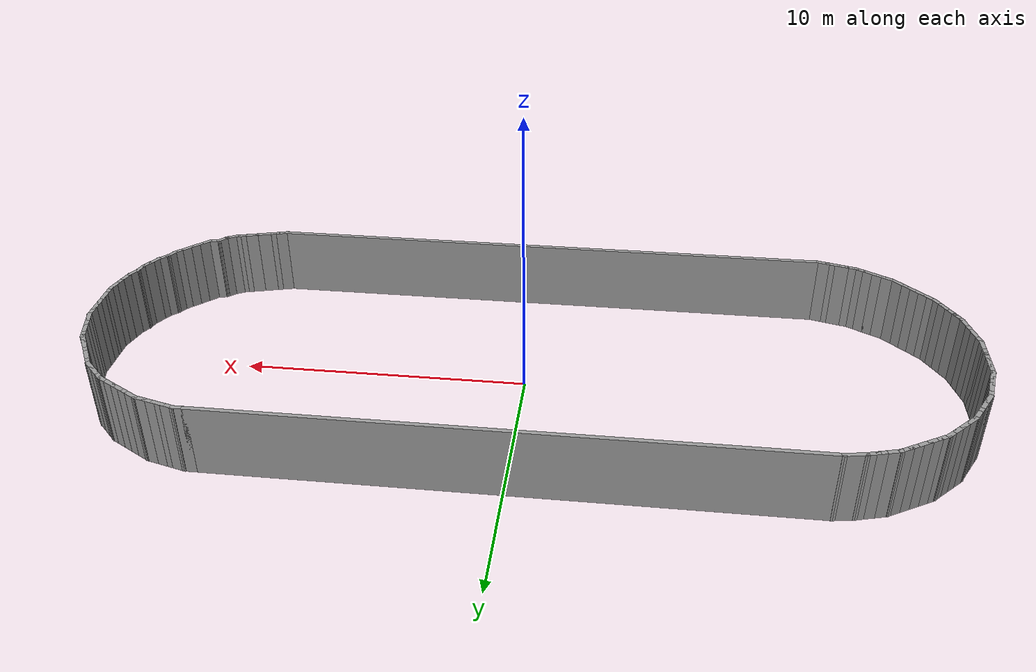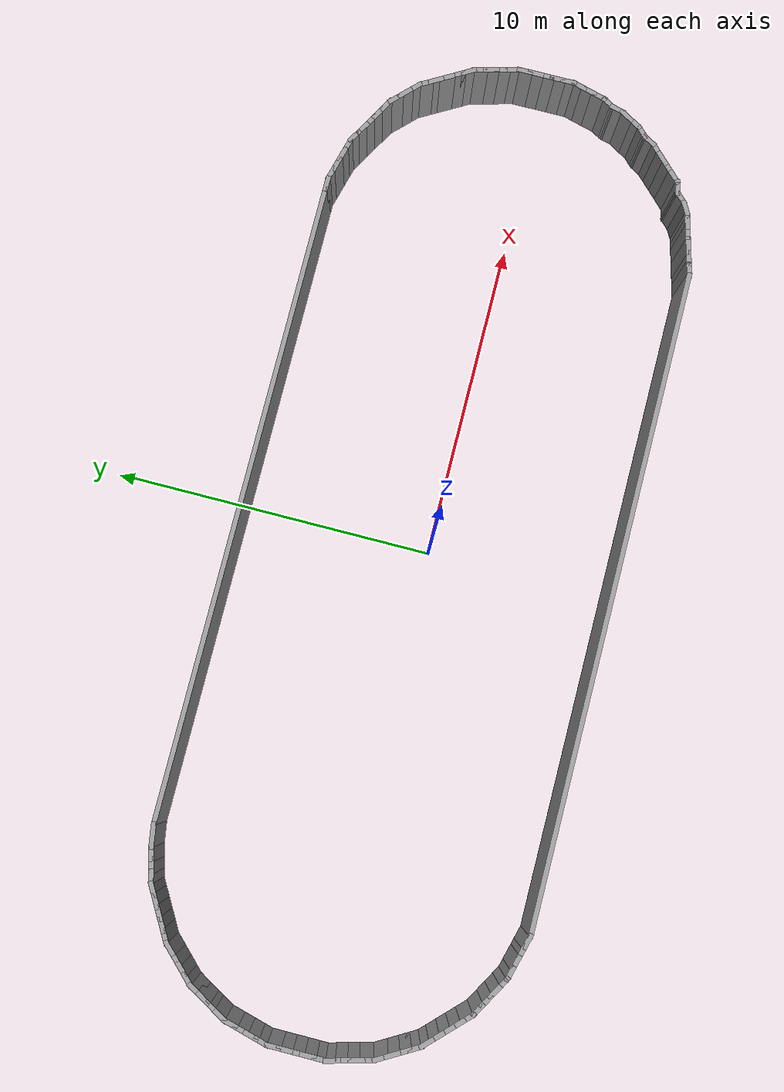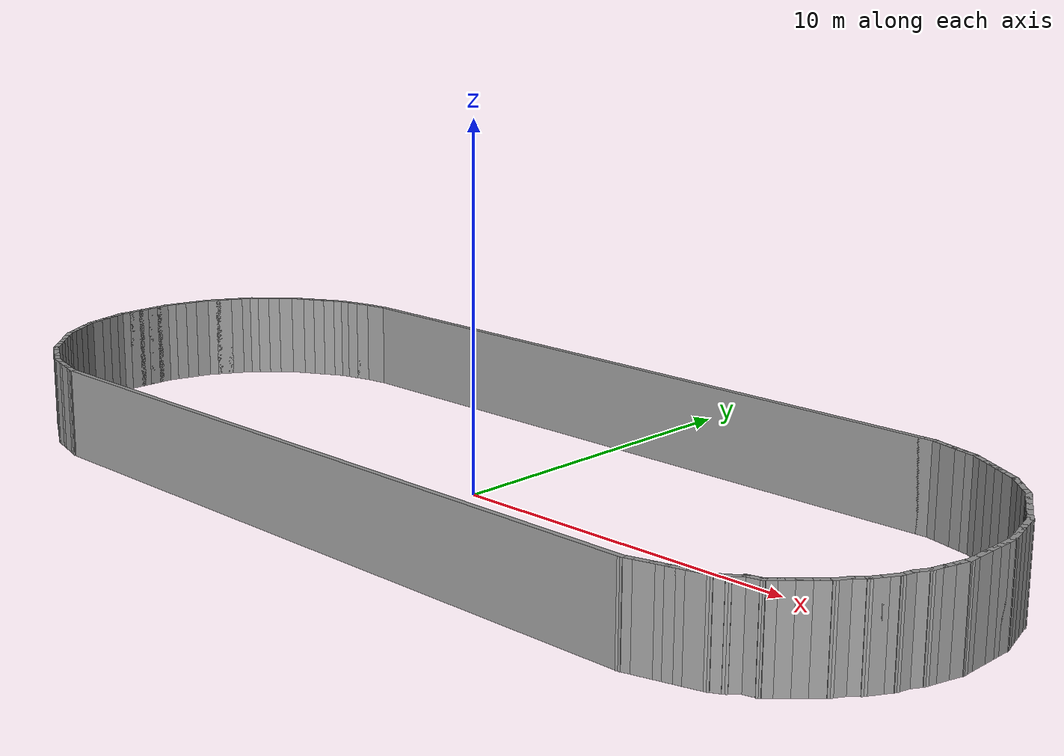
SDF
<?xml version='1.0'?>
<sdf version='1.7'>
  <model name='pool_wall'>
    <pose>-0.108758 0.109657 0 0 -0 0</pose>
    <link name='Wall_0'>
      <collision name='Wall_0_Collision'>
        <geometry>
          <box>
            <size>20 0.15 2.5</size>
          </box>
        </geometry>
        <pose>0 0 1.25 0 -0 0</pose>
      </collision>
      <visual name='Wall_0_Visual'>
        <pose>0 0 1.25 0 -0 0</pose>
        <geometry>
          <box>
            <size>20 0.15 2.5</size>
          </box>
        </geometry>
        <material>
          <script>
            <uri>file://media/materials/scripts/gazebo.material</uri>
            <name>Gazebo/Grey</name>
          </script>
          <ambient>1 1 1 1</ambient>
        </material>
        <meta>
          <layer>0</layer>
        </meta>
      </visual>
      <pose>0.020613 5.7088 0 0 -0 0</pose>
    </link>
    <link name='Wall_1'>
      <collision name='Wall_1_Collision'>
        <geometry>
          <box>
            <size>0.5 0.15 2.5</size>
          </box>
        </geometry>
        <pose>0 0 1.25 0 -0 0</pose>
      </collision>
      <visual name='Wall_1_Visual'>
        <pose>0 0 1.25 0 -0 0</pose>
        <geometry>
          <box>
            <size>0.5 0.15 2.5</size>
          </box>
        </geometry>
        <material>
          <script>
            <uri>file://media/materials/scripts/gazebo.material</uri>
            <name>Gazebo/Grey</name>
          </script>
          <ambient>1 1 1 1</ambient>
        </material>
        <meta>
          <layer>0</layer>
        </meta>
      </visual>
      <pose>10.1206 5.7088 0 0 -0 0</pose>
    </link>
    <link name='Wall_10'>
      <collision name='Wall_10_Collision'>
        <geometry>
          <box>
            <size>0.5 0.15 2.5</size>
          </box>
        </geometry>
        <pose>0 0 1.25 0 -0 0</pose>
      </collision>
      <visual name='Wall_10_Visual'>
        <pose>0 0 1.25 0 -0 0</pose>
        <geometry>
          <box>
            <size>0.5 0.15 2.5</size>
          </box>
        </geometry>
        <material>
          <script>
            <uri>file://media/materials/scripts/gazebo.material</uri>
            <name>Gazebo/Grey</name>
          </script>
          <ambient>1 1 1 1</ambient>
        </material>
        <meta>
          <layer>0</layer>
        </meta>
      </visual>
      <pose>13.0119 4.55895 0 0 -0 -0.523599</pose>
    </link>
    <link name='Wall_100'>
      <collision name='Wall_100_Collision'>
        <geometry>
          <box>
            <size>0.814629 0.15 2.5</size>
          </box>
        </geometry>
        <pose>0 0 1.25 0 -0 0</pose>
      </collision>
      <visual name='Wall_100_Visual'>
        <pose>0 0 1.25 0 -0 0</pose>
        <geometry>
          <box>
            <size>0.814629 0.15 2.5</size>
          </box>
        </geometry>
        <material>
          <script>
            <uri>file://media/materials/scripts/gazebo.material</uri>
            <name>Gazebo/Grey</name>
          </script>
          <ambient>1 1 1 1</ambient>
        </material>
        <meta>
          <layer>0</layer>
        </meta>
      </visual>
      <pose>-10.2328 5.65798 0 0 -0 0.153519</pose>
    </link>
    <link name='Wall_11'>
      <collision name='Wall_11_Collision'>
        <geometry>
          <box>
            <size>0.5 0.15 2.5</size>
          </box>
        </geometry>
        <pose>0 0 1.25 0 -0 0</pose>
      </collision>
      <visual name='Wall_11_Visual'>
        <pose>0 0 1.25 0 -0 0</pose>
        <geometry>
          <box>
            <size>0.5 0.15 2.5</size>
          </box>
        </geometry>
        <material>
          <script>
            <uri>file://media/materials/scripts/gazebo.material</uri>
            <name>Gazebo/Grey</name>
          </script>
          <ambient>1 1 1 1</ambient>
        </material>
        <meta>
          <layer>0</layer>
        </meta>
      </visual>
      <pose>13.2872 4.3477 0 0 -0 -0.785398</pose>
    </link>
    <link name='Wall_12'>
      <collision name='Wall_12_Collision'>
        <geometry>
          <box>
            <size>0.5 0.15 2.5</size>
          </box>
        </geometry>
        <pose>0 0 1.25 0 -0 0</pose>
      </collision>
      <visual name='Wall_12_Visual'>
        <pose>0 0 1.25 0 -0 0</pose>
        <geometry>
          <box>
            <size>0.5 0.15 2.5</size>
          </box>
        </geometry>
        <material>
          <script>
            <uri>file://media/materials/scripts/gazebo.material</uri>
            <name>Gazebo/Grey</name>
          </script>
          <ambient>1 1 1 1</ambient>
        </material>
        <meta>
          <layer>0</layer>
        </meta>
      </visual>
      <pose>13.5347 4.10022 0 0 -0 -0.785398</pose>
    </link>
    <link name='Wall_13'>
      <collision name='Wall_13_Collision'>
        <geometry>
          <box>
            <size>0.5 0.15 2.5</size>
          </box>
        </geometry>
        <pose>0 0 1.25 0 -0 0</pose>
      </collision>
      <visual name='Wall_13_Visual'>
        <pose>0 0 1.25 0 -0 0</pose>
        <geometry>
          <box>
            <size>0.5 0.15 2.5</size>
          </box>
        </geometry>
        <material>
          <script>
            <uri>file://media/materials/scripts/gazebo.material</uri>
            <name>Gazebo/Grey</name>
          </script>
          <ambient>1 1 1 1</ambient>
        </material>
        <meta>
          <layer>0</layer>
        </meta>
      </visual>
      <pose>13.7822 3.85273 0 0 -0 -0.785398</pose>
    </link>
    <link name='Wall_14'>
      <collision name='Wall_14_Collision'>
        <geometry>
          <box>
            <size>0.5 0.15 2.5</size>
          </box>
        </geometry>
        <pose>0 0 1.25 0 -0 0</pose>
      </collision>
      <visual name='Wall_14_Visual'>
        <pose>0 0 1.25 0 -0 0</pose>
        <geometry>
          <box>
            <size>0.5 0.15 2.5</size>
          </box>
        </geometry>
        <material>
          <script>
            <uri>file://media/materials/scripts/gazebo.material</uri>
            <name>Gazebo/Grey</name>
          </script>
          <ambient>1 1 1 1</ambient>
        </material>
        <meta>
          <layer>0</layer>
        </meta>
      </visual>
      <pose>13.9934 3.57743 0 0 -0 -1.0472</pose>
    </link>
    <link name='Wall_15'>
      <collision name='Wall_15_Collision'>
        <geometry>
          <box>
            <size>0.5 0.15 2.5</size>
          </box>
        </geometry>
        <pose>0 0 1.25 0 -0 0</pose>
      </collision>
      <visual name='Wall_15_Visual'>
        <pose>0 0 1.25 0 -0 0</pose>
        <geometry>
          <box>
            <size>0.5 0.15 2.5</size>
          </box>
        </geometry>
        <material>
          <script>
            <uri>file://media/materials/scripts/gazebo.material</uri>
            <name>Gazebo/Grey</name>
          </script>
          <ambient>1 1 1 1</ambient>
        </material>
        <meta>
          <layer>0</layer>
        </meta>
      </visual>
      <pose>14.1684 3.27432 0 0 -0 -1.0472</pose>
    </link>
    <link name='Wall_16'>
      <collision name='Wall_16_Collision'>
        <geometry>
          <box>
            <size>0.5 0.15 2.5</size>
          </box>
        </geometry>
        <pose>0 0 1.25 0 -0 0</pose>
      </collision>
      <visual name='Wall_16_Visual'>
        <pose>0 0 1.25 0 -0 0</pose>
        <geometry>
          <box>
            <size>0.5 0.15 2.5</size>
          </box>
        </geometry>
        <material>
          <script>
            <uri>file://media/materials/scripts/gazebo.material</uri>
            <name>Gazebo/Grey</name>
          </script>
          <ambient>1 1 1 1</ambient>
        </material>
        <meta>
          <layer>0</layer>
        </meta>
      </visual>
      <pose>14.3434 2.97121 0 0 -0 -1.0472</pose>
    </link>
    <link name='Wall_17'>
      <collision name='Wall_17_Collision'>
        <geometry>
          <box>
            <size>0.5 0.15 2.5</size>
          </box>
        </geometry>
        <pose>0 0 1.25 0 -0 0</pose>
      </collision>
      <visual name='Wall_17_Visual'>
        <pose>0 0 1.25 0 -0 0</pose>
        <geometry>
          <box>
            <size>0.5 0.15 2.5</size>
          </box>
        </geometry>
        <material>
          <script>
            <uri>file://media/materials/scripts/gazebo.material</uri>
            <name>Gazebo/Grey</name>
          </script>
          <ambient>1 1 1 1</ambient>
        </material>
        <meta>
          <layer>0</layer>
        </meta>
      </visual>
      <pose>14.5184 2.66811 0 0 -0 -1.0472</pose>
    </link>
    <link name='Wall_18'>
      <collision name='Wall_18_Collision'>
        <geometry>
          <box>
            <size>0.5 0.15 2.5</size>
          </box>
        </geometry>
        <pose>0 0 1.25 0 -0 0</pose>
      </collision>
      <visual name='Wall_18_Visual'>
        <pose>0 0 1.25 0 -0 0</pose>
        <geometry>
          <box>
            <size>0.5 0.15 2.5</size>
          </box>
        </geometry>
        <material>
          <script>
            <uri>file://media/materials/scripts/gazebo.material</uri>
            <name>Gazebo/Grey</name>
          </script>
          <ambient>1 1 1 1</ambient>
        </material>
        <meta>
          <layer>0</layer>
        </meta>
      </visual>
      <pose>14.6934 2.365 0 0 -0 -1.0472</pose>
    </link>
    <link name='Wall_19'>
      <collision name='Wall_19_Collision'>
        <geometry>
          <box>
            <size>0.5 0.15 2.5</size>
          </box>
        </geometry>
        <pose>0 0 1.25 0 -0 0</pose>
      </collision>
      <visual name='Wall_19_Visual'>
        <pose>0 0 1.25 0 -0 0</pose>
        <geometry>
          <box>
            <size>0.5 0.15 2.5</size>
          </box>
        </geometry>
        <material>
          <script>
            <uri>file://media/materials/scripts/gazebo.material</uri>
            <name>Gazebo/Grey</name>
          </script>
          <ambient>1 1 1 1</ambient>
        </material>
        <meta>
          <layer>0</layer>
        </meta>
      </visual>
      <pose>14.8262 2.0444 0 0 -0 -1.309</pose>
    </link>
    <link name='Wall_2'>
      <collision name='Wall_2_Collision'>
        <geometry>
          <box>
            <size>0.5 0.15 2.5</size>
          </box>
        </geometry>
        <pose>0 0 1.25 0 -0 0</pose>
      </collision>
      <visual name='Wall_2_Visual'>
        <pose>0 0 1.25 0 -0 0</pose>
        <geometry>
          <box>
            <size>0.5 0.15 2.5</size>
          </box>
        </geometry>
        <material>
          <script>
            <uri>file://media/materials/scripts/gazebo.material</uri>
            <name>Gazebo/Grey</name>
          </script>
          <ambient>1 1 1 1</ambient>
        </material>
        <meta>
          <layer>0</layer>
        </meta>
      </visual>
      <pose>10.4647 5.6635 0 0 -0 -0.261799</pose>
    </link>
    <link name='Wall_20'>
      <collision name='Wall_20_Collision'>
        <geometry>
          <box>
            <size>0.5 0.15 2.5</size>
          </box>
        </geometry>
        <pose>0 0 1.25 0 -0 0</pose>
      </collision>
      <visual name='Wall_20_Visual'>
        <pose>0 0 1.25 0 -0 0</pose>
        <geometry>
          <box>
            <size>0.5 0.15 2.5</size>
          </box>
        </geometry>
        <material>
          <script>
            <uri>file://media/materials/scripts/gazebo.material</uri>
            <name>Gazebo/Grey</name>
          </script>
          <ambient>1 1 1 1</ambient>
        </material>
        <meta>
          <layer>0</layer>
        </meta>
      </visual>
      <pose>14.9168 1.70633 0 0 -0 -1.309</pose>
    </link>
    <link name='Wall_21'>
      <collision name='Wall_21_Collision'>
        <geometry>
          <box>
            <size>0.5 0.15 2.5</size>
          </box>
        </geometry>
        <pose>0 0 1.25 0 -0 0</pose>
      </collision>
      <visual name='Wall_21_Visual'>
        <pose>0 0 1.25 0 -0 0</pose>
        <geometry>
          <box>
            <size>0.5 0.15 2.5</size>
          </box>
        </geometry>
        <material>
          <script>
            <uri>file://media/materials/scripts/gazebo.material</uri>
            <name>Gazebo/Grey</name>
          </script>
          <ambient>1 1 1 1</ambient>
        </material>
        <meta>
          <layer>0</layer>
        </meta>
      </visual>
      <pose>15.0074 1.36826 0 0 -0 -1.309</pose>
    </link>
    <link name='Wall_22'>
      <collision name='Wall_22_Collision'>
        <geometry>
          <box>
            <size>0.5 0.15 2.5</size>
          </box>
        </geometry>
        <pose>0 0 1.25 0 -0 0</pose>
      </collision>
      <visual name='Wall_22_Visual'>
        <pose>0 0 1.25 0 -0 0</pose>
        <geometry>
          <box>
            <size>0.5 0.15 2.5</size>
          </box>
        </geometry>
        <material>
          <script>
            <uri>file://media/materials/scripts/gazebo.material</uri>
            <name>Gazebo/Grey</name>
          </script>
          <ambient>1 1 1 1</ambient>
        </material>
        <meta>
          <layer>0</layer>
        </meta>
      </visual>
      <pose>15.098 1.03018 0 0 -0 -1.309</pose>
    </link>
    <link name='Wall_23'>
      <collision name='Wall_23_Collision'>
        <geometry>
          <box>
            <size>0.5 0.15 2.5</size>
          </box>
        </geometry>
        <pose>0 0 1.25 0 -0 0</pose>
      </collision>
      <visual name='Wall_23_Visual'>
        <pose>0 0 1.25 0 -0 0</pose>
        <geometry>
          <box>
            <size>0.5 0.15 2.5</size>
          </box>
        </geometry>
        <material>
          <script>
            <uri>file://media/materials/scripts/gazebo.material</uri>
            <name>Gazebo/Grey</name>
          </script>
          <ambient>1 1 1 1</ambient>
        </material>
        <meta>
          <layer>0</layer>
        </meta>
      </visual>
      <pose>15.1433 0.686145 0 0 -0 -1.5708</pose>
    </link>
    <link name='Wall_24'>
      <collision name='Wall_24_Collision'>
        <geometry>
          <box>
            <size>0.5 0.15 2.5</size>
          </box>
        </geometry>
        <pose>0 0 1.25 0 -0 0</pose>
      </collision>
      <visual name='Wall_24_Visual'>
        <pose>0 0 1.25 0 -0 0</pose>
        <geometry>
          <box>
            <size>0.5 0.15 2.5</size>
          </box>
        </geometry>
        <material>
          <script>
            <uri>file://media/materials/scripts/gazebo.material</uri>
            <name>Gazebo/Grey</name>
          </script>
          <ambient>1 1 1 1</ambient>
        </material>
        <meta>
          <layer>0</layer>
        </meta>
      </visual>
      <pose>15.1433 0.336145 0 0 -0 -1.5708</pose>
    </link>
    <link name='Wall_25'>
      <collision name='Wall_25_Collision'>
        <geometry>
          <box>
            <size>0.5 0.15 2.5</size>
          </box>
        </geometry>
        <pose>0 0 1.25 0 -0 0</pose>
      </collision>
      <visual name='Wall_25_Visual'>
        <pose>0 0 1.25 0 -0 0</pose>
        <geometry>
          <box>
            <size>0.5 0.15 2.5</size>
          </box>
        </geometry>
        <material>
          <script>
            <uri>file://media/materials/scripts/gazebo.material</uri>
            <name>Gazebo/Grey</name>
          </script>
          <ambient>1 1 1 1</ambient>
        </material>
        <meta>
          <layer>0</layer>
        </meta>
      </visual>
      <pose>15.1433 -0.013855 0 0 -0 -1.5708</pose>
    </link>
    <link name='Wall_26'>
      <collision name='Wall_26_Collision'>
        <geometry>
          <box>
            <size>0.5 0.15 2.5</size>
          </box>
        </geometry>
        <pose>0 0 1.25 0 -0 0</pose>
      </collision>
      <visual name='Wall_26_Visual'>
        <pose>0 0 1.25 0 -0 0</pose>
        <geometry>
          <box>
            <size>0.5 0.15 2.5</size>
          </box>
        </geometry>
        <material>
          <script>
            <uri>file://media/materials/scripts/gazebo.material</uri>
            <name>Gazebo/Grey</name>
          </script>
          <ambient>1 1 1 1</ambient>
        </material>
        <meta>
          <layer>0</layer>
        </meta>
      </visual>
      <pose>15.1433 -0.363855 0 0 -0 -1.5708</pose>
    </link>
    <link name='Wall_27'>
      <collision name='Wall_27_Collision'>
        <geometry>
          <box>
            <size>0.5 0.15 2.5</size>
          </box>
        </geometry>
        <pose>0 0 1.25 0 -0 0</pose>
      </collision>
      <visual name='Wall_27_Visual'>
        <pose>0 0 1.25 0 -0 0</pose>
        <geometry>
          <box>
            <size>0.5 0.15 2.5</size>
          </box>
        </geometry>
        <material>
          <script>
            <uri>file://media/materials/scripts/gazebo.material</uri>
            <name>Gazebo/Grey</name>
          </script>
          <ambient>1 1 1 1</ambient>
        </material>
        <meta>
          <layer>0</layer>
        </meta>
      </visual>
      <pose>15.1433 -0.713855 0 0 -0 -1.5708</pose>
    </link>
    <link name='Wall_28'>
      <collision name='Wall_28_Collision'>
        <geometry>
          <box>
            <size>0.5 0.15 2.5</size>
          </box>
        </geometry>
        <pose>0 0 1.25 0 -0 0</pose>
      </collision>
      <visual name='Wall_28_Visual'>
        <pose>0 0 1.25 0 -0 0</pose>
        <geometry>
          <box>
            <size>0.5 0.15 2.5</size>
          </box>
        </geometry>
        <material>
          <script>
            <uri>file://media/materials/scripts/gazebo.material</uri>
            <name>Gazebo/Grey</name>
          </script>
          <ambient>1 1 1 1</ambient>
        </material>
        <meta>
          <layer>0</layer>
        </meta>
      </visual>
      <pose>15.098 -1.05789 0 0 -0 -1.8326</pose>
    </link>
    <link name='Wall_29'>
      <collision name='Wall_29_Collision'>
        <geometry>
          <box>
            <size>0.5 0.15 2.5</size>
          </box>
        </geometry>
        <pose>0 0 1.25 0 -0 0</pose>
      </collision>
      <visual name='Wall_29_Visual'>
        <pose>0 0 1.25 0 -0 0</pose>
        <geometry>
          <box>
            <size>0.5 0.15 2.5</size>
          </box>
        </geometry>
        <material>
          <script>
            <uri>file://media/materials/scripts/gazebo.material</uri>
            <name>Gazebo/Grey</name>
          </script>
          <ambient>1 1 1 1</ambient>
        </material>
        <meta>
          <layer>0</layer>
        </meta>
      </visual>
      <pose>15.0074 -1.39597 0 0 -0 -1.8326</pose>
    </link>
    <link name='Wall_3'>
      <collision name='Wall_3_Collision'>
        <geometry>
          <box>
            <size>0.5 0.15 2.5</size>
          </box>
        </geometry>
        <pose>0 0 1.25 0 -0 0</pose>
      </collision>
      <visual name='Wall_3_Visual'>
        <pose>0 0 1.25 0 -0 0</pose>
        <geometry>
          <box>
            <size>0.5 0.15 2.5</size>
          </box>
        </geometry>
        <material>
          <script>
            <uri>file://media/materials/scripts/gazebo.material</uri>
            <name>Gazebo/Grey</name>
          </script>
          <ambient>1 1 1 1</ambient>
        </material>
        <meta>
          <layer>0</layer>
        </meta>
      </visual>
      <pose>10.8027 5.57292 0 0 -0 -0.261799</pose>
    </link>
    <link name='Wall_30'>
      <collision name='Wall_30_Collision'>
        <geometry>
          <box>
            <size>0.5 0.15 2.5</size>
          </box>
        </geometry>
        <pose>0 0 1.25 0 -0 0</pose>
      </collision>
      <visual name='Wall_30_Visual'>
        <pose>0 0 1.25 0 -0 0</pose>
        <geometry>
          <box>
            <size>0.5 0.15 2.5</size>
          </box>
        </geometry>
        <material>
          <script>
            <uri>file://media/materials/scripts/gazebo.material</uri>
            <name>Gazebo/Grey</name>
          </script>
          <ambient>1 1 1 1</ambient>
        </material>
        <meta>
          <layer>0</layer>
        </meta>
      </visual>
      <pose>14.9168 -1.73404 0 0 -0 -1.8326</pose>
    </link>
    <link name='Wall_31'>
      <collision name='Wall_31_Collision'>
        <geometry>
          <box>
            <size>0.5 0.15 2.5</size>
          </box>
        </geometry>
        <pose>0 0 1.25 0 -0 0</pose>
      </collision>
      <visual name='Wall_31_Visual'>
        <pose>0 0 1.25 0 -0 0</pose>
        <geometry>
          <box>
            <size>0.5 0.15 2.5</size>
          </box>
        </geometry>
        <material>
          <script>
            <uri>file://media/materials/scripts/gazebo.material</uri>
            <name>Gazebo/Grey</name>
          </script>
          <ambient>1 1 1 1</ambient>
        </material>
        <meta>
          <layer>0</layer>
        </meta>
      </visual>
      <pose>14.784 -2.05463 0 0 -0 -2.0944</pose>
    </link>
    <link name='Wall_32'>
      <collision name='Wall_32_Collision'>
        <geometry>
          <box>
            <size>0.5 0.15 2.5</size>
          </box>
        </geometry>
        <pose>0 0 1.25 0 -0 0</pose>
      </collision>
      <visual name='Wall_32_Visual'>
        <pose>0 0 1.25 0 -0 0</pose>
        <geometry>
          <box>
            <size>0.5 0.15 2.5</size>
          </box>
        </geometry>
        <material>
          <script>
            <uri>file://media/materials/scripts/gazebo.material</uri>
            <name>Gazebo/Grey</name>
          </script>
          <ambient>1 1 1 1</ambient>
        </material>
        <meta>
          <layer>0</layer>
        </meta>
      </visual>
      <pose>14.6512 -2.37522 0 0 -0 -1.8326</pose>
    </link>
    <link name='Wall_33'>
      <collision name='Wall_33_Collision'>
        <geometry>
          <box>
            <size>0.5 0.15 2.5</size>
          </box>
        </geometry>
        <pose>0 0 1.25 0 -0 0</pose>
      </collision>
      <visual name='Wall_33_Visual'>
        <pose>0 0 1.25 0 -0 0</pose>
        <geometry>
          <box>
            <size>0.5 0.15 2.5</size>
          </box>
        </geometry>
        <material>
          <script>
            <uri>file://media/materials/scripts/gazebo.material</uri>
            <name>Gazebo/Grey</name>
          </script>
          <ambient>1 1 1 1</ambient>
        </material>
        <meta>
          <layer>0</layer>
        </meta>
      </visual>
      <pose>14.5184 -2.69581 0 0 -0 -2.0944</pose>
    </link>
    <link name='Wall_34'>
      <collision name='Wall_34_Collision'>
        <geometry>
          <box>
            <size>0.5 0.15 2.5</size>
          </box>
        </geometry>
        <pose>0 0 1.25 0 -0 0</pose>
      </collision>
      <visual name='Wall_34_Visual'>
        <pose>0 0 1.25 0 -0 0</pose>
        <geometry>
          <box>
            <size>0.5 0.15 2.5</size>
          </box>
        </geometry>
        <material>
          <script>
            <uri>file://media/materials/scripts/gazebo.material</uri>
            <name>Gazebo/Grey</name>
          </script>
          <ambient>1 1 1 1</ambient>
        </material>
        <meta>
          <layer>0</layer>
        </meta>
      </visual>
      <pose>14.3434 -2.99892 0 0 -0 -2.0944</pose>
    </link>
    <link name='Wall_35'>
      <collision name='Wall_35_Collision'>
        <geometry>
          <box>
            <size>0.5 0.15 2.5</size>
          </box>
        </geometry>
        <pose>0 0 1.25 0 -0 0</pose>
      </collision>
      <visual name='Wall_35_Visual'>
        <pose>0 0 1.25 0 -0 0</pose>
        <geometry>
          <box>
            <size>0.5 0.15 2.5</size>
          </box>
        </geometry>
        <material>
          <script>
            <uri>file://media/materials/scripts/gazebo.material</uri>
            <name>Gazebo/Grey</name>
          </script>
          <ambient>1 1 1 1</ambient>
        </material>
        <meta>
          <layer>0</layer>
        </meta>
      </visual>
      <pose>14.1322 -3.27422 0 0 -0 -2.35619</pose>
    </link>
    <link name='Wall_36'>
      <collision name='Wall_36_Collision'>
        <geometry>
          <box>
            <size>0.5 0.15 2.5</size>
          </box>
        </geometry>
        <pose>0 0 1.25 0 -0 0</pose>
      </collision>
      <visual name='Wall_36_Visual'>
        <pose>0 0 1.25 0 -0 0</pose>
        <geometry>
          <box>
            <size>0.5 0.15 2.5</size>
          </box>
        </geometry>
        <material>
          <script>
            <uri>file://media/materials/scripts/gazebo.material</uri>
            <name>Gazebo/Grey</name>
          </script>
          <ambient>1 1 1 1</ambient>
        </material>
        <meta>
          <layer>0</layer>
        </meta>
      </visual>
      <pose>13.9209 -3.54952 0 0 -0 -2.0944</pose>
    </link>
    <link name='Wall_37'>
      <collision name='Wall_37_Collision'>
        <geometry>
          <box>
            <size>0.5 0.15 2.5</size>
          </box>
        </geometry>
        <pose>0 0 1.25 0 -0 0</pose>
      </collision>
      <visual name='Wall_37_Visual'>
        <pose>0 0 1.25 0 -0 0</pose>
        <geometry>
          <box>
            <size>0.5 0.15 2.5</size>
          </box>
        </geometry>
        <material>
          <script>
            <uri>file://media/materials/scripts/gazebo.material</uri>
            <name>Gazebo/Grey</name>
          </script>
          <ambient>1 1 1 1</ambient>
        </material>
        <meta>
          <layer>0</layer>
        </meta>
      </visual>
      <pose>13.7097 -3.82482 0 0 -0 -2.35619</pose>
    </link>
    <link name='Wall_38'>
      <collision name='Wall_38_Collision'>
        <geometry>
          <box>
            <size>0.5 0.15 2.5</size>
          </box>
        </geometry>
        <pose>0 0 1.25 0 -0 0</pose>
      </collision>
      <visual name='Wall_38_Visual'>
        <pose>0 0 1.25 0 -0 0</pose>
        <geometry>
          <box>
            <size>0.5 0.15 2.5</size>
          </box>
        </geometry>
        <material>
          <script>
            <uri>file://media/materials/scripts/gazebo.material</uri>
            <name>Gazebo/Grey</name>
          </script>
          <ambient>1 1 1 1</ambient>
        </material>
        <meta>
          <layer>0</layer>
        </meta>
      </visual>
      <pose>13.4622 -4.07231 0 0 -0 -2.35619</pose>
    </link>
    <link name='Wall_39'>
      <collision name='Wall_39_Collision'>
        <geometry>
          <box>
            <size>0.5 0.15 2.5</size>
          </box>
        </geometry>
        <pose>0 0 1.25 0 -0 0</pose>
      </collision>
      <visual name='Wall_39_Visual'>
        <pose>0 0 1.25 0 -0 0</pose>
        <geometry>
          <box>
            <size>0.5 0.15 2.5</size>
          </box>
        </geometry>
        <material>
          <script>
            <uri>file://media/materials/scripts/gazebo.material</uri>
            <name>Gazebo/Grey</name>
          </script>
          <ambient>1 1 1 1</ambient>
        </material>
        <meta>
          <layer>0</layer>
        </meta>
      </visual>
      <pose>13.2147 -4.31979 0 0 -0 -2.35619</pose>
    </link>
    <link name='Wall_4'>
      <collision name='Wall_4_Collision'>
        <geometry>
          <box>
            <size>0.5 0.15 2.5</size>
          </box>
        </geometry>
        <pose>0 0 1.25 0 -0 0</pose>
      </collision>
      <visual name='Wall_4_Visual'>
        <pose>0 0 1.25 0 -0 0</pose>
        <geometry>
          <box>
            <size>0.5 0.15 2.5</size>
          </box>
        </geometry>
        <material>
          <script>
            <uri>file://media/materials/scripts/gazebo.material</uri>
            <name>Gazebo/Grey</name>
          </script>
          <ambient>1 1 1 1</ambient>
        </material>
        <meta>
          <layer>0</layer>
        </meta>
      </visual>
      <pose>11.1408 5.48233 0 0 -0 -0.261799</pose>
    </link>
    <link name='Wall_40'>
      <collision name='Wall_40_Collision'>
        <geometry>
          <box>
            <size>0.5 0.15 2.5</size>
          </box>
        </geometry>
        <pose>0 0 1.25 0 -0 0</pose>
      </collision>
      <visual name='Wall_40_Visual'>
        <pose>0 0 1.25 0 -0 0</pose>
        <geometry>
          <box>
            <size>0.5 0.15 2.5</size>
          </box>
        </geometry>
        <material>
          <script>
            <uri>file://media/materials/scripts/gazebo.material</uri>
            <name>Gazebo/Grey</name>
          </script>
          <ambient>1 1 1 1</ambient>
        </material>
        <meta>
          <layer>0</layer>
        </meta>
      </visual>
      <pose>12.9672 -4.56728 0 0 -0 -2.35619</pose>
    </link>
    <link name='Wall_41'>
      <collision name='Wall_41_Collision'>
        <geometry>
          <box>
            <size>0.5 0.15 2.5</size>
          </box>
        </geometry>
        <pose>0 0 1.25 0 -0 0</pose>
      </collision>
      <visual name='Wall_41_Visual'>
        <pose>0 0 1.25 0 -0 0</pose>
        <geometry>
          <box>
            <size>0.5 0.15 2.5</size>
          </box>
        </geometry>
        <material>
          <script>
            <uri>file://media/materials/scripts/gazebo.material</uri>
            <name>Gazebo/Grey</name>
          </script>
          <ambient>1 1 1 1</ambient>
        </material>
        <meta>
          <layer>0</layer>
        </meta>
      </visual>
      <pose>12.6744 -4.73632 0 0 -0 -2.87979</pose>
    </link>
    <link name='Wall_42'>
      <collision name='Wall_42_Collision'>
        <geometry>
          <box>
            <size>0.5 0.15 2.5</size>
          </box>
        </geometry>
        <pose>0 0 1.25 0 -0 0</pose>
      </collision>
      <visual name='Wall_42_Visual'>
        <pose>0 0 1.25 0 -0 0</pose>
        <geometry>
          <box>
            <size>0.5 0.15 2.5</size>
          </box>
        </geometry>
        <material>
          <script>
            <uri>file://media/materials/scripts/gazebo.material</uri>
            <name>Gazebo/Grey</name>
          </script>
          <ambient>1 1 1 1</ambient>
        </material>
        <meta>
          <layer>0</layer>
        </meta>
      </visual>
      <pose>12.3817 -4.90535 0 0 -0 -2.35619</pose>
    </link>
    <link name='Wall_43'>
      <collision name='Wall_43_Collision'>
        <geometry>
          <box>
            <size>0.5 0.15 2.5</size>
          </box>
        </geometry>
        <pose>0 0 1.25 0 -0 0</pose>
      </collision>
      <visual name='Wall_43_Visual'>
        <pose>0 0 1.25 0 -0 0</pose>
        <geometry>
          <box>
            <size>0.5 0.15 2.5</size>
          </box>
        </geometry>
        <material>
          <script>
            <uri>file://media/materials/scripts/gazebo.material</uri>
            <name>Gazebo/Grey</name>
          </script>
          <ambient>1 1 1 1</ambient>
        </material>
        <meta>
          <layer>0</layer>
        </meta>
      </visual>
      <pose>12.1064 -5.1166 0 0 -0 -2.61799</pose>
    </link>
    <link name='Wall_44'>
      <collision name='Wall_44_Collision'>
        <geometry>
          <box>
            <size>0.25 0.15 2.5</size>
          </box>
        </geometry>
        <pose>0 0 1.25 0 -0 0</pose>
      </collision>
      <visual name='Wall_44_Visual'>
        <pose>0 0 1.25 0 -0 0</pose>
        <geometry>
          <box>
            <size>0.25 0.15 2.5</size>
          </box>
        </geometry>
        <material>
          <script>
            <uri>file://media/materials/scripts/gazebo.material</uri>
            <name>Gazebo/Grey</name>
          </script>
          <ambient>1 1 1 1</ambient>
        </material>
        <meta>
          <layer>0</layer>
        </meta>
      </visual>
      <pose>11.9065 -5.21704 0 0 -0 -2.87979</pose>
    </link>
    <link name='Wall_45'>
      <collision name='Wall_45_Collision'>
        <geometry>
          <box>
            <size>0.5 0.15 2.5</size>
          </box>
        </geometry>
        <pose>0 0 1.25 0 -0 0</pose>
      </collision>
      <visual name='Wall_45_Visual'>
        <pose>0 0 1.25 0 -0 0</pose>
        <geometry>
          <box>
            <size>0.5 0.15 2.5</size>
          </box>
        </geometry>
        <material>
          <script>
            <uri>file://media/materials/scripts/gazebo.material</uri>
            <name>Gazebo/Grey</name>
          </script>
          <ambient>1 1 1 1</ambient>
        </material>
        <meta>
          <layer>0</layer>
        </meta>
      </visual>
      <pose>11.6892 -5.27527 0 0 -0 -2.87979</pose>
    </link>
    <link name='Wall_46'>
      <collision name='Wall_46_Collision'>
        <geometry>
          <box>
            <size>0.5 0.15 2.5</size>
          </box>
        </geometry>
        <pose>0 0 1.25 0 -0 0</pose>
      </collision>
      <visual name='Wall_46_Visual'>
        <pose>0 0 1.25 0 -0 0</pose>
        <geometry>
          <box>
            <size>0.5 0.15 2.5</size>
          </box>
        </geometry>
        <material>
          <script>
            <uri>file://media/materials/scripts/gazebo.material</uri>
            <name>Gazebo/Grey</name>
          </script>
          <ambient>1 1 1 1</ambient>
        </material>
        <meta>
          <layer>0</layer>
        </meta>
      </visual>
      <pose>11.3511 -5.36586 0 0 -0 -2.87979</pose>
    </link>
    <link name='Wall_47'>
      <collision name='Wall_47_Collision'>
        <geometry>
          <box>
            <size>0.25 0.15 2.5</size>
          </box>
        </geometry>
        <pose>0 0 1.25 0 -0 0</pose>
      </collision>
      <visual name='Wall_47_Visual'>
        <pose>0 0 1.25 0 -0 0</pose>
        <geometry>
          <box>
            <size>0.25 0.15 2.5</size>
          </box>
        </geometry>
        <material>
          <script>
            <uri>file://media/materials/scripts/gazebo.material</uri>
            <name>Gazebo/Grey</name>
          </script>
          <ambient>1 1 1 1</ambient>
        </material>
        <meta>
          <layer>0</layer>
        </meta>
      </visual>
      <pose>11.1338 -5.42409 0 0 -0 -2.87979</pose>
    </link>
    <link name='Wall_48'>
      <collision name='Wall_48_Collision'>
        <geometry>
          <box>
            <size>0.5 0.15 2.5</size>
          </box>
        </geometry>
        <pose>0 0 1.25 0 -0 0</pose>
      </collision>
      <visual name='Wall_48_Visual'>
        <pose>0 0 1.25 0 -0 0</pose>
        <geometry>
          <box>
            <size>0.5 0.15 2.5</size>
          </box>
        </geometry>
        <material>
          <script>
            <uri>file://media/materials/scripts/gazebo.material</uri>
            <name>Gazebo/Grey</name>
          </script>
          <ambient>1 1 1 1</ambient>
        </material>
        <meta>
          <layer>0</layer>
        </meta>
      </visual>
      <pose>10.9164 -5.48233 0 0 -0 -2.87979</pose>
    </link>
    <link name='Wall_49'>
      <collision name='Wall_49_Collision'>
        <geometry>
          <box>
            <size>0.5 0.15 2.5</size>
          </box>
        </geometry>
        <pose>0 0 1.25 0 -0 0</pose>
      </collision>
      <visual name='Wall_49_Visual'>
        <pose>0 0 1.25 0 -0 0</pose>
        <geometry>
          <box>
            <size>0.5 0.15 2.5</size>
          </box>
        </geometry>
        <material>
          <script>
            <uri>file://media/materials/scripts/gazebo.material</uri>
            <name>Gazebo/Grey</name>
          </script>
          <ambient>1 1 1 1</ambient>
        </material>
        <meta>
          <layer>0</layer>
        </meta>
      </visual>
      <pose>10.5784 -5.57292 0 0 -0 -2.87979</pose>
    </link>
    <link name='Wall_5'>
      <collision name='Wall_5_Collision'>
        <geometry>
          <box>
            <size>0.5 0.15 2.5</size>
          </box>
        </geometry>
        <pose>0 0 1.25 0 -0 0</pose>
      </collision>
      <visual name='Wall_5_Visual'>
        <pose>0 0 1.25 0 -0 0</pose>
        <geometry>
          <box>
            <size>0.5 0.15 2.5</size>
          </box>
        </geometry>
        <material>
          <script>
            <uri>file://media/materials/scripts/gazebo.material</uri>
            <name>Gazebo/Grey</name>
          </script>
          <ambient>1 1 1 1</ambient>
        </material>
        <meta>
          <layer>0</layer>
        </meta>
      </visual>
      <pose>11.4789 5.39174 0 0 -0 -0.261799</pose>
    </link>
    <link name='Wall_50'>
      <collision name='Wall_50_Collision'>
        <geometry>
          <box>
            <size>0.5 0.15 2.5</size>
          </box>
        </geometry>
        <pose>0 0 1.25 0 -0 0</pose>
      </collision>
      <visual name='Wall_50_Visual'>
        <pose>0 0 1.25 0 -0 0</pose>
        <geometry>
          <box>
            <size>0.5 0.15 2.5</size>
          </box>
        </geometry>
        <material>
          <script>
            <uri>file://media/materials/scripts/gazebo.material</uri>
            <name>Gazebo/Grey</name>
          </script>
          <ambient>1 1 1 1</ambient>
        </material>
        <meta>
          <layer>0</layer>
        </meta>
      </visual>
      <pose>10.2403 -5.6635 0 0 -0 -2.87979</pose>
    </link>
    <link name='Wall_51'>
      <collision name='Wall_51_Collision'>
        <geometry>
          <box>
            <size>20.5 0.15 2.5</size>
          </box>
        </geometry>
        <pose>0 0 1.25 0 -0 0</pose>
      </collision>
      <visual name='Wall_51_Visual'>
        <pose>0 0 1.25 0 -0 0</pose>
        <geometry>
          <box>
            <size>20.5 0.15 2.5</size>
          </box>
        </geometry>
        <material>
          <script>
            <uri>file://media/materials/scripts/gazebo.material</uri>
            <name>Gazebo/Grey</name>
          </script>
          <ambient>1 1 1 1</ambient>
        </material>
        <meta>
          <layer>0</layer>
        </meta>
      </visual>
      <pose>-0.103747 -5.7088 0 0 -0 3.14159</pose>
    </link>
    <link name='Wall_52'>
      <collision name='Wall_52_Collision'>
        <geometry>
          <box>
            <size>0.5 0.15 2.5</size>
          </box>
        </geometry>
        <pose>0 0 1.25 0 -0 0</pose>
      </collision>
      <visual name='Wall_52_Visual'>
        <pose>0 0 1.25 0 -0 0</pose>
        <geometry>
          <box>
            <size>0.5 0.15 2.5</size>
          </box>
        </geometry>
        <material>
          <script>
            <uri>file://media/materials/scripts/gazebo.material</uri>
            <name>Gazebo/Grey</name>
          </script>
          <ambient>1 1 1 1</ambient>
        </material>
        <meta>
          <layer>0</layer>
        </meta>
      </visual>
      <pose>-10.4478 -5.6635 0 0 -0 2.87979</pose>
    </link>
    <link name='Wall_53'>
      <collision name='Wall_53_Collision'>
        <geometry>
          <box>
            <size>0.5 0.15 2.5</size>
          </box>
        </geometry>
        <pose>0 0 1.25 0 -0 0</pose>
      </collision>
      <visual name='Wall_53_Visual'>
        <pose>0 0 1.25 0 -0 0</pose>
        <geometry>
          <box>
            <size>0.5 0.15 2.5</size>
          </box>
        </geometry>
        <material>
          <script>
            <uri>file://media/materials/scripts/gazebo.material</uri>
            <name>Gazebo/Grey</name>
          </script>
          <ambient>1 1 1 1</ambient>
        </material>
        <meta>
          <layer>0</layer>
        </meta>
      </visual>
      <pose>-10.7859 -5.57292 0 0 -0 2.87979</pose>
    </link>
    <link name='Wall_54'>
      <collision name='Wall_54_Collision'>
        <geometry>
          <box>
            <size>0.5 0.15 2.5</size>
          </box>
        </geometry>
        <pose>0 0 1.25 0 -0 0</pose>
      </collision>
      <visual name='Wall_54_Visual'>
        <pose>0 0 1.25 0 -0 0</pose>
        <geometry>
          <box>
            <size>0.5 0.15 2.5</size>
          </box>
        </geometry>
        <material>
          <script>
            <uri>file://media/materials/scripts/gazebo.material</uri>
            <name>Gazebo/Grey</name>
          </script>
          <ambient>1 1 1 1</ambient>
        </material>
        <meta>
          <layer>0</layer>
        </meta>
      </visual>
      <pose>-11.1239 -5.48233 0 0 -0 2.87979</pose>
    </link>
    <link name='Wall_55'>
      <collision name='Wall_55_Collision'>
        <geometry>
          <box>
            <size>0.5 0.15 2.5</size>
          </box>
        </geometry>
        <pose>0 0 1.25 0 -0 0</pose>
      </collision>
      <visual name='Wall_55_Visual'>
        <pose>0 0 1.25 0 -0 0</pose>
        <geometry>
          <box>
            <size>0.5 0.15 2.5</size>
          </box>
        </geometry>
        <material>
          <script>
            <uri>file://media/materials/scripts/gazebo.material</uri>
            <name>Gazebo/Grey</name>
          </script>
          <ambient>1 1 1 1</ambient>
        </material>
        <meta>
          <layer>0</layer>
        </meta>
      </visual>
      <pose>-11.462 -5.39174 0 0 -0 2.87979</pose>
    </link>
    <link name='Wall_56'>
      <collision name='Wall_56_Collision'>
        <geometry>
          <box>
            <size>0.5 0.15 2.5</size>
          </box>
        </geometry>
        <pose>0 0 1.25 0 -0 0</pose>
      </collision>
      <visual name='Wall_56_Visual'>
        <pose>0 0 1.25 0 -0 0</pose>
        <geometry>
          <box>
            <size>0.5 0.15 2.5</size>
          </box>
        </geometry>
        <material>
          <script>
            <uri>file://media/materials/scripts/gazebo.material</uri>
            <name>Gazebo/Grey</name>
          </script>
          <ambient>1 1 1 1</ambient>
        </material>
        <meta>
          <layer>0</layer>
        </meta>
      </visual>
      <pose>-11.7826 -5.25895 0 0 -0 2.61799</pose>
    </link>
    <link name='Wall_57'>
      <collision name='Wall_57_Collision'>
        <geometry>
          <box>
            <size>0.5 0.15 2.5</size>
          </box>
        </geometry>
        <pose>0 0 1.25 0 -0 0</pose>
      </collision>
      <visual name='Wall_57_Visual'>
        <pose>0 0 1.25 0 -0 0</pose>
        <geometry>
          <box>
            <size>0.5 0.15 2.5</size>
          </box>
        </geometry>
        <material>
          <script>
            <uri>file://media/materials/scripts/gazebo.material</uri>
            <name>Gazebo/Grey</name>
          </script>
          <ambient>1 1 1 1</ambient>
        </material>
        <meta>
          <layer>0</layer>
        </meta>
      </visual>
      <pose>-12.0857 -5.08395 0 0 -0 2.61799</pose>
    </link>
    <link name='Wall_58'>
      <collision name='Wall_58_Collision'>
        <geometry>
          <box>
            <size>0.5 0.15 2.5</size>
          </box>
        </geometry>
        <pose>0 0 1.25 0 -0 0</pose>
      </collision>
      <visual name='Wall_58_Visual'>
        <pose>0 0 1.25 0 -0 0</pose>
        <geometry>
          <box>
            <size>0.5 0.15 2.5</size>
          </box>
        </geometry>
        <material>
          <script>
            <uri>file://media/materials/scripts/gazebo.material</uri>
            <name>Gazebo/Grey</name>
          </script>
          <ambient>1 1 1 1</ambient>
        </material>
        <meta>
          <layer>0</layer>
        </meta>
      </visual>
      <pose>-12.3888 -4.90895 0 0 -0 2.61799</pose>
    </link>
    <link name='Wall_59'>
      <collision name='Wall_59_Collision'>
        <geometry>
          <box>
            <size>0.5 0.15 2.5</size>
          </box>
        </geometry>
        <pose>0 0 1.25 0 -0 0</pose>
      </collision>
      <visual name='Wall_59_Visual'>
        <pose>0 0 1.25 0 -0 0</pose>
        <geometry>
          <box>
            <size>0.5 0.15 2.5</size>
          </box>
        </geometry>
        <material>
          <script>
            <uri>file://media/materials/scripts/gazebo.material</uri>
            <name>Gazebo/Grey</name>
          </script>
          <ambient>1 1 1 1</ambient>
        </material>
        <meta>
          <layer>0</layer>
        </meta>
      </visual>
      <pose>-12.6919 -4.73395 0 0 -0 2.61799</pose>
    </link>
    <link name='Wall_6'>
      <collision name='Wall_6_Collision'>
        <geometry>
          <box>
            <size>0.5 0.15 2.5</size>
          </box>
        </geometry>
        <pose>0 0 1.25 0 -0 0</pose>
      </collision>
      <visual name='Wall_6_Visual'>
        <pose>0 0 1.25 0 -0 0</pose>
        <geometry>
          <box>
            <size>0.5 0.15 2.5</size>
          </box>
        </geometry>
        <material>
          <script>
            <uri>file://media/materials/scripts/gazebo.material</uri>
            <name>Gazebo/Grey</name>
          </script>
          <ambient>1 1 1 1</ambient>
        </material>
        <meta>
          <layer>0</layer>
        </meta>
      </visual>
      <pose>11.7995 5.25895 0 0 -0 -0.523599</pose>
    </link>
    <link name='Wall_60'>
      <collision name='Wall_60_Collision'>
        <geometry>
          <box>
            <size>0.5 0.15 2.5</size>
          </box>
        </geometry>
        <pose>0 0 1.25 0 -0 0</pose>
      </collision>
      <visual name='Wall_60_Visual'>
        <pose>0 0 1.25 0 -0 0</pose>
        <geometry>
          <box>
            <size>0.5 0.15 2.5</size>
          </box>
        </geometry>
        <material>
          <script>
            <uri>file://media/materials/scripts/gazebo.material</uri>
            <name>Gazebo/Grey</name>
          </script>
          <ambient>1 1 1 1</ambient>
        </material>
        <meta>
          <layer>0</layer>
        </meta>
      </visual>
      <pose>-12.9672 -4.5227 0 0 -0 2.35619</pose>
    </link>
    <link name='Wall_61'>
      <collision name='Wall_61_Collision'>
        <geometry>
          <box>
            <size>0.5 0.15 2.5</size>
          </box>
        </geometry>
        <pose>0 0 1.25 0 -0 0</pose>
      </collision>
      <visual name='Wall_61_Visual'>
        <pose>0 0 1.25 0 -0 0</pose>
        <geometry>
          <box>
            <size>0.5 0.15 2.5</size>
          </box>
        </geometry>
        <material>
          <script>
            <uri>file://media/materials/scripts/gazebo.material</uri>
            <name>Gazebo/Grey</name>
          </script>
          <ambient>1 1 1 1</ambient>
        </material>
        <meta>
          <layer>0</layer>
        </meta>
      </visual>
      <pose>-13.2147 -4.27522 0 0 -0 2.35619</pose>
    </link>
    <link name='Wall_62'>
      <collision name='Wall_62_Collision'>
        <geometry>
          <box>
            <size>0.5 0.15 2.5</size>
          </box>
        </geometry>
        <pose>0 0 1.25 0 -0 0</pose>
      </collision>
      <visual name='Wall_62_Visual'>
        <pose>0 0 1.25 0 -0 0</pose>
        <geometry>
          <box>
            <size>0.5 0.15 2.5</size>
          </box>
        </geometry>
        <material>
          <script>
            <uri>file://media/materials/scripts/gazebo.material</uri>
            <name>Gazebo/Grey</name>
          </script>
          <ambient>1 1 1 1</ambient>
        </material>
        <meta>
          <layer>0</layer>
        </meta>
      </visual>
      <pose>-13.4622 -4.02773 0 0 -0 2.35619</pose>
    </link>
    <link name='Wall_63'>
      <collision name='Wall_63_Collision'>
        <geometry>
          <box>
            <size>0.5 0.15 2.5</size>
          </box>
        </geometry>
        <pose>0 0 1.25 0 -0 0</pose>
      </collision>
      <visual name='Wall_63_Visual'>
        <pose>0 0 1.25 0 -0 0</pose>
        <geometry>
          <box>
            <size>0.5 0.15 2.5</size>
          </box>
        </geometry>
        <material>
          <script>
            <uri>file://media/materials/scripts/gazebo.material</uri>
            <name>Gazebo/Grey</name>
          </script>
          <ambient>1 1 1 1</ambient>
        </material>
        <meta>
          <layer>0</layer>
        </meta>
      </visual>
      <pose>-13.7097 -3.78024 0 0 -0 2.35619</pose>
    </link>
    <link name='Wall_64'>
      <collision name='Wall_64_Collision'>
        <geometry>
          <box>
            <size>0.5 0.15 2.5</size>
          </box>
        </geometry>
        <pose>0 0 1.25 0 -0 0</pose>
      </collision>
      <visual name='Wall_64_Visual'>
        <pose>0 0 1.25 0 -0 0</pose>
        <geometry>
          <box>
            <size>0.5 0.15 2.5</size>
          </box>
        </geometry>
        <material>
          <script>
            <uri>file://media/materials/scripts/gazebo.material</uri>
            <name>Gazebo/Grey</name>
          </script>
          <ambient>1 1 1 1</ambient>
        </material>
        <meta>
          <layer>0</layer>
        </meta>
      </visual>
      <pose>-13.9572 -3.53275 0 0 -0 2.35619</pose>
    </link>
    <link name='Wall_65'>
      <collision name='Wall_65_Collision'>
        <geometry>
          <box>
            <size>0.5 0.15 2.5</size>
          </box>
        </geometry>
        <pose>0 0 1.25 0 -0 0</pose>
      </collision>
      <visual name='Wall_65_Visual'>
        <pose>0 0 1.25 0 -0 0</pose>
        <geometry>
          <box>
            <size>0.5 0.15 2.5</size>
          </box>
        </geometry>
        <material>
          <script>
            <uri>file://media/materials/scripts/gazebo.material</uri>
            <name>Gazebo/Grey</name>
          </script>
          <ambient>1 1 1 1</ambient>
        </material>
        <meta>
          <layer>0</layer>
        </meta>
      </visual>
      <pose>-14.1684 -3.25746 0 0 -0 2.0944</pose>
    </link>
    <link name='Wall_68'>
      <collision name='Wall_68_Collision'>
        <geometry>
          <box>
            <size>0.5 0.15 2.5</size>
          </box>
        </geometry>
        <pose>0 0 1.25 0 -0 0</pose>
      </collision>
      <visual name='Wall_68_Visual'>
        <pose>0 0 1.25 0 -0 0</pose>
        <geometry>
          <box>
            <size>0.5 0.15 2.5</size>
          </box>
        </geometry>
        <material>
          <script>
            <uri>file://media/materials/scripts/gazebo.material</uri>
            <name>Gazebo/Grey</name>
          </script>
          <ambient>1 1 1 1</ambient>
        </material>
        <meta>
          <layer>0</layer>
        </meta>
      </visual>
      <pose>-14.3434 -2.95435 0 0 -0 2.0944</pose>
    </link>
    <link name='Wall_69'>
      <collision name='Wall_69_Collision'>
        <geometry>
          <box>
            <size>0.5 0.15 2.5</size>
          </box>
        </geometry>
        <pose>0 0 1.25 0 -0 0</pose>
      </collision>
      <visual name='Wall_69_Visual'>
        <pose>0 0 1.25 0 -0 0</pose>
        <geometry>
          <box>
            <size>0.5 0.15 2.5</size>
          </box>
        </geometry>
        <material>
          <script>
            <uri>file://media/materials/scripts/gazebo.material</uri>
            <name>Gazebo/Grey</name>
          </script>
          <ambient>1 1 1 1</ambient>
        </material>
        <meta>
          <layer>0</layer>
        </meta>
      </visual>
      <pose>-14.5184 -2.65124 0 0 -0 2.0944</pose>
    </link>
    <link name='Wall_7'>
      <collision name='Wall_7_Collision'>
        <geometry>
          <box>
            <size>0.5 0.15 2.5</size>
          </box>
        </geometry>
        <pose>0 0 1.25 0 -0 0</pose>
      </collision>
      <visual name='Wall_7_Visual'>
        <pose>0 0 1.25 0 -0 0</pose>
        <geometry>
          <box>
            <size>0.5 0.15 2.5</size>
          </box>
        </geometry>
        <material>
          <script>
            <uri>file://media/materials/scripts/gazebo.material</uri>
            <name>Gazebo/Grey</name>
          </script>
          <ambient>1 1 1 1</ambient>
        </material>
        <meta>
          <layer>0</layer>
        </meta>
      </visual>
      <pose>12.1026 5.08395 0 0 -0 -0.523599</pose>
    </link>
    <link name='Wall_70'>
      <collision name='Wall_70_Collision'>
        <geometry>
          <box>
            <size>0.5 0.15 2.5</size>
          </box>
        </geometry>
        <pose>0 0 1.25 0 -0 0</pose>
      </collision>
      <visual name='Wall_70_Visual'>
        <pose>0 0 1.25 0 -0 0</pose>
        <geometry>
          <box>
            <size>0.5 0.15 2.5</size>
          </box>
        </geometry>
        <material>
          <script>
            <uri>file://media/materials/scripts/gazebo.material</uri>
            <name>Gazebo/Grey</name>
          </script>
          <ambient>1 1 1 1</ambient>
        </material>
        <meta>
          <layer>0</layer>
        </meta>
      </visual>
      <pose>-14.6934 -2.34813 0 0 -0 2.0944</pose>
    </link>
    <link name='Wall_71'>
      <collision name='Wall_71_Collision'>
        <geometry>
          <box>
            <size>0.5 0.15 2.5</size>
          </box>
        </geometry>
        <pose>0 0 1.25 0 -0 0</pose>
      </collision>
      <visual name='Wall_71_Visual'>
        <pose>0 0 1.25 0 -0 0</pose>
        <geometry>
          <box>
            <size>0.5 0.15 2.5</size>
          </box>
        </geometry>
        <material>
          <script>
            <uri>file://media/materials/scripts/gazebo.material</uri>
            <name>Gazebo/Grey</name>
          </script>
          <ambient>1 1 1 1</ambient>
        </material>
        <meta>
          <layer>0</layer>
        </meta>
      </visual>
      <pose>-14.8262 -2.02754 0 0 -0 1.8326</pose>
    </link>
    <link name='Wall_72'>
      <collision name='Wall_72_Collision'>
        <geometry>
          <box>
            <size>0.5 0.15 2.5</size>
          </box>
        </geometry>
        <pose>0 0 1.25 0 -0 0</pose>
      </collision>
      <visual name='Wall_72_Visual'>
        <pose>0 0 1.25 0 -0 0</pose>
        <geometry>
          <box>
            <size>0.5 0.15 2.5</size>
          </box>
        </geometry>
        <material>
          <script>
            <uri>file://media/materials/scripts/gazebo.material</uri>
            <name>Gazebo/Grey</name>
          </script>
          <ambient>1 1 1 1</ambient>
        </material>
        <meta>
          <layer>0</layer>
        </meta>
      </visual>
      <pose>-14.9168 -1.68946 0 0 -0 1.8326</pose>
    </link>
    <link name='Wall_73'>
      <collision name='Wall_73_Collision'>
        <geometry>
          <box>
            <size>0.5 0.15 2.5</size>
          </box>
        </geometry>
        <pose>0 0 1.25 0 -0 0</pose>
      </collision>
      <visual name='Wall_73_Visual'>
        <pose>0 0 1.25 0 -0 0</pose>
        <geometry>
          <box>
            <size>0.5 0.15 2.5</size>
          </box>
        </geometry>
        <material>
          <script>
            <uri>file://media/materials/scripts/gazebo.material</uri>
            <name>Gazebo/Grey</name>
          </script>
          <ambient>1 1 1 1</ambient>
        </material>
        <meta>
          <layer>0</layer>
        </meta>
      </visual>
      <pose>-15.0074 -1.35139 0 0 -0 1.8326</pose>
    </link>
    <link name='Wall_74'>
      <collision name='Wall_74_Collision'>
        <geometry>
          <box>
            <size>0.5 0.15 2.5</size>
          </box>
        </geometry>
        <pose>0 0 1.25 0 -0 0</pose>
      </collision>
      <visual name='Wall_74_Visual'>
        <pose>0 0 1.25 0 -0 0</pose>
        <geometry>
          <box>
            <size>0.5 0.15 2.5</size>
          </box>
        </geometry>
        <material>
          <script>
            <uri>file://media/materials/scripts/gazebo.material</uri>
            <name>Gazebo/Grey</name>
          </script>
          <ambient>1 1 1 1</ambient>
        </material>
        <meta>
          <layer>0</layer>
        </meta>
      </visual>
      <pose>-15.098 -1.01332 0 0 -0 1.8326</pose>
    </link>
    <link name='Wall_75'>
      <collision name='Wall_75_Collision'>
        <geometry>
          <box>
            <size>0.5 0.15 2.5</size>
          </box>
        </geometry>
        <pose>0 0 1.25 0 -0 0</pose>
      </collision>
      <visual name='Wall_75_Visual'>
        <pose>0 0 1.25 0 -0 0</pose>
        <geometry>
          <box>
            <size>0.5 0.15 2.5</size>
          </box>
        </geometry>
        <material>
          <script>
            <uri>file://media/materials/scripts/gazebo.material</uri>
            <name>Gazebo/Grey</name>
          </script>
          <ambient>1 1 1 1</ambient>
        </material>
        <meta>
          <layer>0</layer>
        </meta>
      </visual>
      <pose>-15.1433 -0.669279 0 0 -0 1.5708</pose>
    </link>
    <link name='Wall_76'>
      <collision name='Wall_76_Collision'>
        <geometry>
          <box>
            <size>0.5 0.15 2.5</size>
          </box>
        </geometry>
        <pose>0 0 1.25 0 -0 0</pose>
      </collision>
      <visual name='Wall_76_Visual'>
        <pose>0 0 1.25 0 -0 0</pose>
        <geometry>
          <box>
            <size>0.5 0.15 2.5</size>
          </box>
        </geometry>
        <material>
          <script>
            <uri>file://media/materials/scripts/gazebo.material</uri>
            <name>Gazebo/Grey</name>
          </script>
          <ambient>1 1 1 1</ambient>
        </material>
        <meta>
          <layer>0</layer>
        </meta>
      </visual>
      <pose>-15.1433 -0.319279 0 0 -0 1.5708</pose>
    </link>
    <link name='Wall_77'>
      <collision name='Wall_77_Collision'>
        <geometry>
          <box>
            <size>0.5 0.15 2.5</size>
          </box>
        </geometry>
        <pose>0 0 1.25 0 -0 0</pose>
      </collision>
      <visual name='Wall_77_Visual'>
        <pose>0 0 1.25 0 -0 0</pose>
        <geometry>
          <box>
            <size>0.5 0.15 2.5</size>
          </box>
        </geometry>
        <material>
          <script>
            <uri>file://media/materials/scripts/gazebo.material</uri>
            <name>Gazebo/Grey</name>
          </script>
          <ambient>1 1 1 1</ambient>
        </material>
        <meta>
          <layer>0</layer>
        </meta>
      </visual>
      <pose>-15.1433 0.030721 0 0 -0 1.5708</pose>
    </link>
    <link name='Wall_78'>
      <collision name='Wall_78_Collision'>
        <geometry>
          <box>
            <size>0.5 0.15 2.5</size>
          </box>
        </geometry>
        <pose>0 0 1.25 0 -0 0</pose>
      </collision>
      <visual name='Wall_78_Visual'>
        <pose>0 0 1.25 0 -0 0</pose>
        <geometry>
          <box>
            <size>0.5 0.15 2.5</size>
          </box>
        </geometry>
        <material>
          <script>
            <uri>file://media/materials/scripts/gazebo.material</uri>
            <name>Gazebo/Grey</name>
          </script>
          <ambient>1 1 1 1</ambient>
        </material>
        <meta>
          <layer>0</layer>
        </meta>
      </visual>
      <pose>-15.1433 0.380721 0 0 -0 1.5708</pose>
    </link>
    <link name='Wall_79'>
      <collision name='Wall_79_Collision'>
        <geometry>
          <box>
            <size>0.5 0.15 2.5</size>
          </box>
        </geometry>
        <pose>0 0 1.25 0 -0 0</pose>
      </collision>
      <visual name='Wall_79_Visual'>
        <pose>0 0 1.25 0 -0 0</pose>
        <geometry>
          <box>
            <size>0.5 0.15 2.5</size>
          </box>
        </geometry>
        <material>
          <script>
            <uri>file://media/materials/scripts/gazebo.material</uri>
            <name>Gazebo/Grey</name>
          </script>
          <ambient>1 1 1 1</ambient>
        </material>
        <meta>
          <layer>0</layer>
        </meta>
      </visual>
      <pose>-15.1433 0.730721 0 0 -0 1.5708</pose>
    </link>
    <link name='Wall_8'>
      <collision name='Wall_8_Collision'>
        <geometry>
          <box>
            <size>0.5 0.15 2.5</size>
          </box>
        </geometry>
        <pose>0 0 1.25 0 -0 0</pose>
      </collision>
      <visual name='Wall_8_Visual'>
        <pose>0 0 1.25 0 -0 0</pose>
        <geometry>
          <box>
            <size>0.5 0.15 2.5</size>
          </box>
        </geometry>
        <material>
          <script>
            <uri>file://media/materials/scripts/gazebo.material</uri>
            <name>Gazebo/Grey</name>
          </script>
          <ambient>1 1 1 1</ambient>
        </material>
        <meta>
          <layer>0</layer>
        </meta>
      </visual>
      <pose>12.4057 4.90895 0 0 -0 -0.523599</pose>
    </link>
    <link name='Wall_80'>
      <collision name='Wall_80_Collision'>
        <geometry>
          <box>
            <size>0.5 0.15 2.5</size>
          </box>
        </geometry>
        <pose>0 0 1.25 0 -0 0</pose>
      </collision>
      <visual name='Wall_80_Visual'>
        <pose>0 0 1.25 0 -0 0</pose>
        <geometry>
          <box>
            <size>0.5 0.15 2.5</size>
          </box>
        </geometry>
        <material>
          <script>
            <uri>file://media/materials/scripts/gazebo.material</uri>
            <name>Gazebo/Grey</name>
          </script>
          <ambient>1 1 1 1</ambient>
        </material>
        <meta>
          <layer>0</layer>
        </meta>
      </visual>
      <pose>-15.098 1.07476 0 0 -0 1.309</pose>
    </link>
    <link name='Wall_81'>
      <collision name='Wall_81_Collision'>
        <geometry>
          <box>
            <size>0.5 0.15 2.5</size>
          </box>
        </geometry>
        <pose>0 0 1.25 0 -0 0</pose>
      </collision>
      <visual name='Wall_81_Visual'>
        <pose>0 0 1.25 0 -0 0</pose>
        <geometry>
          <box>
            <size>0.5 0.15 2.5</size>
          </box>
        </geometry>
        <material>
          <script>
            <uri>file://media/materials/scripts/gazebo.material</uri>
            <name>Gazebo/Grey</name>
          </script>
          <ambient>1 1 1 1</ambient>
        </material>
        <meta>
          <layer>0</layer>
        </meta>
      </visual>
      <pose>-15.0074 1.41283 0 0 -0 1.309</pose>
    </link>
    <link name='Wall_82'>
      <collision name='Wall_82_Collision'>
        <geometry>
          <box>
            <size>0.5 0.15 2.5</size>
          </box>
        </geometry>
        <pose>0 0 1.25 0 -0 0</pose>
      </collision>
      <visual name='Wall_82_Visual'>
        <pose>0 0 1.25 0 -0 0</pose>
        <geometry>
          <box>
            <size>0.5 0.15 2.5</size>
          </box>
        </geometry>
        <material>
          <script>
            <uri>file://media/materials/scripts/gazebo.material</uri>
            <name>Gazebo/Grey</name>
          </script>
          <ambient>1 1 1 1</ambient>
        </material>
        <meta>
          <layer>0</layer>
        </meta>
      </visual>
      <pose>-14.9168 1.75091 0 0 -0 1.309</pose>
    </link>
    <link name='Wall_83'>
      <collision name='Wall_83_Collision'>
        <geometry>
          <box>
            <size>0.5 0.15 2.5</size>
          </box>
        </geometry>
        <pose>0 0 1.25 0 -0 0</pose>
      </collision>
      <visual name='Wall_83_Visual'>
        <pose>0 0 1.25 0 -0 0</pose>
        <geometry>
          <box>
            <size>0.5 0.15 2.5</size>
          </box>
        </geometry>
        <material>
          <script>
            <uri>file://media/materials/scripts/gazebo.material</uri>
            <name>Gazebo/Grey</name>
          </script>
          <ambient>1 1 1 1</ambient>
        </material>
        <meta>
          <layer>0</layer>
        </meta>
      </visual>
      <pose>-14.8262 2.08898 0 0 -0 1.309</pose>
    </link>
    <link name='Wall_84'>
      <collision name='Wall_84_Collision'>
        <geometry>
          <box>
            <size>0.5 0.15 2.5</size>
          </box>
        </geometry>
        <pose>0 0 1.25 0 -0 0</pose>
      </collision>
      <visual name='Wall_84_Visual'>
        <pose>0 0 1.25 0 -0 0</pose>
        <geometry>
          <box>
            <size>0.5 0.15 2.5</size>
          </box>
        </geometry>
        <material>
          <script>
            <uri>file://media/materials/scripts/gazebo.material</uri>
            <name>Gazebo/Grey</name>
          </script>
          <ambient>1 1 1 1</ambient>
        </material>
        <meta>
          <layer>0</layer>
        </meta>
      </visual>
      <pose>-14.6934 2.40957 0 0 -0 1.0472</pose>
    </link>
    <link name='Wall_85'>
      <collision name='Wall_85_Collision'>
        <geometry>
          <box>
            <size>0.5 0.15 2.5</size>
          </box>
        </geometry>
        <pose>0 0 1.25 0 -0 0</pose>
      </collision>
      <visual name='Wall_85_Visual'>
        <pose>0 0 1.25 0 -0 0</pose>
        <geometry>
          <box>
            <size>0.5 0.15 2.5</size>
          </box>
        </geometry>
        <material>
          <script>
            <uri>file://media/materials/scripts/gazebo.material</uri>
            <name>Gazebo/Grey</name>
          </script>
          <ambient>1 1 1 1</ambient>
        </material>
        <meta>
          <layer>0</layer>
        </meta>
      </visual>
      <pose>-14.5184 2.71268 0 0 -0 1.0472</pose>
    </link>
    <link name='Wall_86'>
      <collision name='Wall_86_Collision'>
        <geometry>
          <box>
            <size>0.5 0.15 2.5</size>
          </box>
        </geometry>
        <pose>0 0 1.25 0 -0 0</pose>
      </collision>
      <visual name='Wall_86_Visual'>
        <pose>0 0 1.25 0 -0 0</pose>
        <geometry>
          <box>
            <size>0.5 0.15 2.5</size>
          </box>
        </geometry>
        <material>
          <script>
            <uri>file://media/materials/scripts/gazebo.material</uri>
            <name>Gazebo/Grey</name>
          </script>
          <ambient>1 1 1 1</ambient>
        </material>
        <meta>
          <layer>0</layer>
        </meta>
      </visual>
      <pose>-14.3434 3.01579 0 0 -0 1.0472</pose>
    </link>
    <link name='Wall_87'>
      <collision name='Wall_87_Collision'>
        <geometry>
          <box>
            <size>0.5 0.15 2.5</size>
          </box>
        </geometry>
        <pose>0 0 1.25 0 -0 0</pose>
      </collision>
      <visual name='Wall_87_Visual'>
        <pose>0 0 1.25 0 -0 0</pose>
        <geometry>
          <box>
            <size>0.5 0.15 2.5</size>
          </box>
        </geometry>
        <material>
          <script>
            <uri>file://media/materials/scripts/gazebo.material</uri>
            <name>Gazebo/Grey</name>
          </script>
          <ambient>1 1 1 1</ambient>
        </material>
        <meta>
          <layer>0</layer>
        </meta>
      </visual>
      <pose>-14.1684 3.3189 0 0 -0 1.0472</pose>
    </link>
    <link name='Wall_88'>
      <collision name='Wall_88_Collision'>
        <geometry>
          <box>
            <size>0.5 0.15 2.5</size>
          </box>
        </geometry>
        <pose>0 0 1.25 0 -0 0</pose>
      </collision>
      <visual name='Wall_88_Visual'>
        <pose>0 0 1.25 0 -0 0</pose>
        <geometry>
          <box>
            <size>0.5 0.15 2.5</size>
          </box>
        </geometry>
        <material>
          <script>
            <uri>file://media/materials/scripts/gazebo.material</uri>
            <name>Gazebo/Grey</name>
          </script>
          <ambient>1 1 1 1</ambient>
        </material>
        <meta>
          <layer>0</layer>
        </meta>
      </visual>
      <pose>-13.9572 3.5942 0 0 -0 0.785398</pose>
    </link>
    <link name='Wall_89'>
      <collision name='Wall_89_Collision'>
        <geometry>
          <box>
            <size>0.5 0.15 2.5</size>
          </box>
        </geometry>
        <pose>0 0 1.25 0 -0 0</pose>
      </collision>
      <visual name='Wall_89_Visual'>
        <pose>0 0 1.25 0 -0 0</pose>
        <geometry>
          <box>
            <size>0.5 0.15 2.5</size>
          </box>
        </geometry>
        <material>
          <script>
            <uri>file://media/materials/scripts/gazebo.material</uri>
            <name>Gazebo/Grey</name>
          </script>
          <ambient>1 1 1 1</ambient>
        </material>
        <meta>
          <layer>0</layer>
        </meta>
      </visual>
      <pose>-13.7097 3.84168 0 0 -0 0.785398</pose>
    </link>
    <link name='Wall_9'>
      <collision name='Wall_9_Collision'>
        <geometry>
          <box>
            <size>0.5 0.15 2.5</size>
          </box>
        </geometry>
        <pose>0 0 1.25 0 -0 0</pose>
      </collision>
      <visual name='Wall_9_Visual'>
        <pose>0 0 1.25 0 -0 0</pose>
        <geometry>
          <box>
            <size>0.5 0.15 2.5</size>
          </box>
        </geometry>
        <material>
          <script>
            <uri>file://media/materials/scripts/gazebo.material</uri>
            <name>Gazebo/Grey</name>
          </script>
          <ambient>1 1 1 1</ambient>
        </material>
        <meta>
          <layer>0</layer>
        </meta>
      </visual>
      <pose>12.7088 4.73395 0 0 -0 -0.523599</pose>
    </link>
    <link name='Wall_90'>
      <collision name='Wall_90_Collision'>
        <geometry>
          <box>
            <size>0.5 0.15 2.5</size>
          </box>
        </geometry>
        <pose>0 0 1.25 0 -0 0</pose>
      </collision>
      <visual name='Wall_90_Visual'>
        <pose>0 0 1.25 0 -0 0</pose>
        <geometry>
          <box>
            <size>0.5 0.15 2.5</size>
          </box>
        </geometry>
        <material>
          <script>
            <uri>file://media/materials/scripts/gazebo.material</uri>
            <name>Gazebo/Grey</name>
          </script>
          <ambient>1 1 1 1</ambient>
        </material>
        <meta>
          <layer>0</layer>
        </meta>
      </visual>
      <pose>-13.4622 4.08917 0 0 -0 0.785398</pose>
    </link>
    <link name='Wall_91'>
      <collision name='Wall_91_Collision'>
        <geometry>
          <box>
            <size>0.5 0.15 2.5</size>
          </box>
        </geometry>
        <pose>0 0 1.25 0 -0 0</pose>
      </collision>
      <visual name='Wall_91_Visual'>
        <pose>0 0 1.25 0 -0 0</pose>
        <geometry>
          <box>
            <size>0.5 0.15 2.5</size>
          </box>
        </geometry>
        <material>
          <script>
            <uri>file://media/materials/scripts/gazebo.material</uri>
            <name>Gazebo/Grey</name>
          </script>
          <ambient>1 1 1 1</ambient>
        </material>
        <meta>
          <layer>0</layer>
        </meta>
      </visual>
      <pose>-13.2147 4.33666 0 0 -0 0.785398</pose>
    </link>
    <link name='Wall_92'>
      <collision name='Wall_92_Collision'>
        <geometry>
          <box>
            <size>0.5 0.15 2.5</size>
          </box>
        </geometry>
        <pose>0 0 1.25 0 -0 0</pose>
      </collision>
      <visual name='Wall_92_Visual'>
        <pose>0 0 1.25 0 -0 0</pose>
        <geometry>
          <box>
            <size>0.5 0.15 2.5</size>
          </box>
        </geometry>
        <material>
          <script>
            <uri>file://media/materials/scripts/gazebo.material</uri>
            <name>Gazebo/Grey</name>
          </script>
          <ambient>1 1 1 1</ambient>
        </material>
        <meta>
          <layer>0</layer>
        </meta>
      </visual>
      <pose>-12.9394 4.5479 0 0 -0 0.523599</pose>
    </link>
    <link name='Wall_93'>
      <collision name='Wall_93_Collision'>
        <geometry>
          <box>
            <size>0.5 0.15 2.5</size>
          </box>
        </geometry>
        <pose>0 0 1.25 0 -0 0</pose>
      </collision>
      <visual name='Wall_93_Visual'>
        <pose>0 0 1.25 0 -0 0</pose>
        <geometry>
          <box>
            <size>0.5 0.15 2.5</size>
          </box>
        </geometry>
        <material>
          <script>
            <uri>file://media/materials/scripts/gazebo.material</uri>
            <name>Gazebo/Grey</name>
          </script>
          <ambient>1 1 1 1</ambient>
        </material>
        <meta>
          <layer>0</layer>
        </meta>
      </visual>
      <pose>-12.6363 4.7229 0 0 -0 0.523599</pose>
    </link>
    <link name='Wall_94'>
      <collision name='Wall_94_Collision'>
        <geometry>
          <box>
            <size>0.5 0.15 2.5</size>
          </box>
        </geometry>
        <pose>0 0 1.25 0 -0 0</pose>
      </collision>
      <visual name='Wall_94_Visual'>
        <pose>0 0 1.25 0 -0 0</pose>
        <geometry>
          <box>
            <size>0.5 0.15 2.5</size>
          </box>
        </geometry>
        <material>
          <script>
            <uri>file://media/materials/scripts/gazebo.material</uri>
            <name>Gazebo/Grey</name>
          </script>
          <ambient>1 1 1 1</ambient>
        </material>
        <meta>
          <layer>0</layer>
        </meta>
      </visual>
      <pose>-12.3332 4.8979 0 0 -0 0.523599</pose>
    </link>
    <link name='Wall_95'>
      <collision name='Wall_95_Collision'>
        <geometry>
          <box>
            <size>0.5 0.15 2.5</size>
          </box>
        </geometry>
        <pose>0 0 1.25 0 -0 0</pose>
      </collision>
      <visual name='Wall_95_Visual'>
        <pose>0 0 1.25 0 -0 0</pose>
        <geometry>
          <box>
            <size>0.5 0.15 2.5</size>
          </box>
        </geometry>
        <material>
          <script>
            <uri>file://media/materials/scripts/gazebo.material</uri>
            <name>Gazebo/Grey</name>
          </script>
          <ambient>1 1 1 1</ambient>
        </material>
        <meta>
          <layer>0</layer>
        </meta>
      </visual>
      <pose>-12.0301 5.0729 0 0 -0 0.523599</pose>
    </link>
    <link name='Wall_96'>
      <collision name='Wall_96_Collision'>
        <geometry>
          <box>
            <size>0.5 0.15 2.5</size>
          </box>
        </geometry>
        <pose>0 0 1.25 0 -0 0</pose>
      </collision>
      <visual name='Wall_96_Visual'>
        <pose>0 0 1.25 0 -0 0</pose>
        <geometry>
          <box>
            <size>0.5 0.15 2.5</size>
          </box>
        </geometry>
        <material>
          <script>
            <uri>file://media/materials/scripts/gazebo.material</uri>
            <name>Gazebo/Grey</name>
          </script>
          <ambient>1 1 1 1</ambient>
        </material>
        <meta>
          <layer>0</layer>
        </meta>
      </visual>
      <pose>-11.727 5.2479 0 0 -0 0.523599</pose>
    </link>
    <link name='Wall_97'>
      <collision name='Wall_97_Collision'>
        <geometry>
          <box>
            <size>0.5 0.15 2.5</size>
          </box>
        </geometry>
        <pose>0 0 1.25 0 -0 0</pose>
      </collision>
      <visual name='Wall_97_Visual'>
        <pose>0 0 1.25 0 -0 0</pose>
        <geometry>
          <box>
            <size>0.5 0.15 2.5</size>
          </box>
        </geometry>
        <material>
          <script>
            <uri>file://media/materials/scripts/gazebo.material</uri>
            <name>Gazebo/Grey</name>
          </script>
          <ambient>1 1 1 1</ambient>
        </material>
        <meta>
          <layer>0</layer>
        </meta>
      </visual>
      <pose>-11.4064 5.3807 0 0 -0 0.261799</pose>
    </link>
    <link name='Wall_98'>
      <collision name='Wall_98_Collision'>
        <geometry>
          <box>
            <size>0.5 0.15 2.5</size>
          </box>
        </geometry>
        <pose>0 0 1.25 0 -0 0</pose>
      </collision>
      <visual name='Wall_98_Visual'>
        <pose>0 0 1.25 0 -0 0</pose>
        <geometry>
          <box>
            <size>0.5 0.15 2.5</size>
          </box>
        </geometry>
        <material>
          <script>
            <uri>file://media/materials/scripts/gazebo.material</uri>
            <name>Gazebo/Grey</name>
          </script>
          <ambient>1 1 1 1</ambient>
        </material>
        <meta>
          <layer>0</layer>
        </meta>
      </visual>
      <pose>-11.0683 5.47128 0 0 -0 0.261799</pose>
    </link>
    <link name='Wall_99'>
      <collision name='Wall_99_Collision'>
        <geometry>
          <box>
            <size>0.5 0.15 2.5</size>
          </box>
        </geometry>
        <pose>0 0 1.25 0 -0 0</pose>
      </collision>
      <visual name='Wall_99_Visual'>
        <pose>0 0 1.25 0 -0 0</pose>
        <geometry>
          <box>
            <size>0.5 0.15 2.5</size>
          </box>
        </geometry>
        <material>
          <script>
            <uri>file://media/materials/scripts/gazebo.material</uri>
            <name>Gazebo/Grey</name>
          </script>
          <ambient>1 1 1 1</ambient>
        </material>
        <meta>
          <layer>0</layer>
        </meta>
      </visual>
      <pose>-10.7302 5.56187 0 0 -0 0.261799</pose>
    </link>
    <static>1</static>
  </model>
</sdf>
